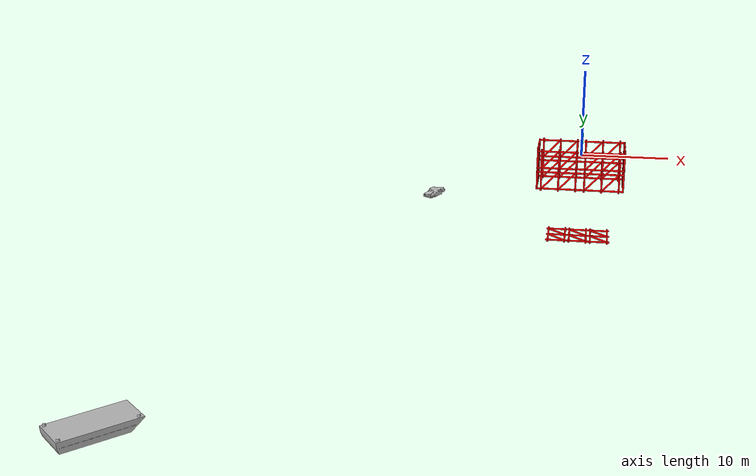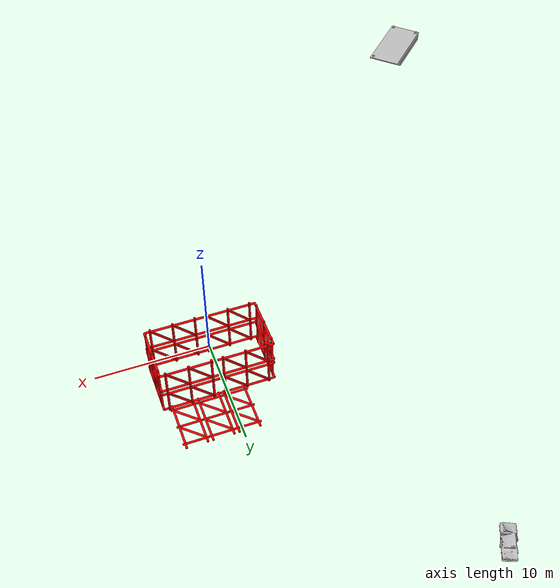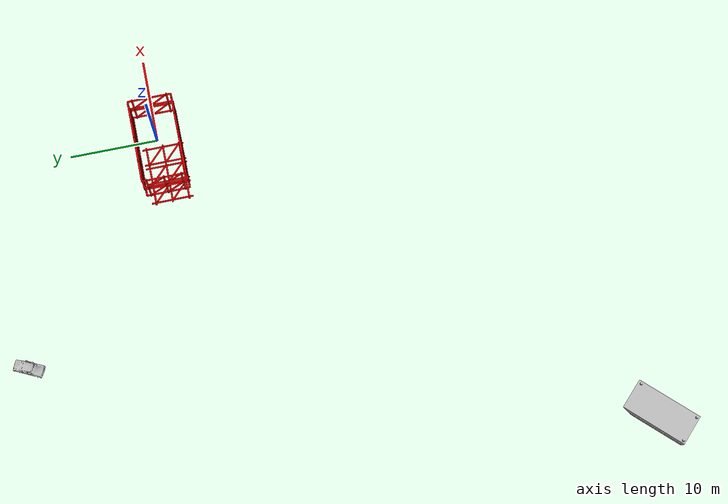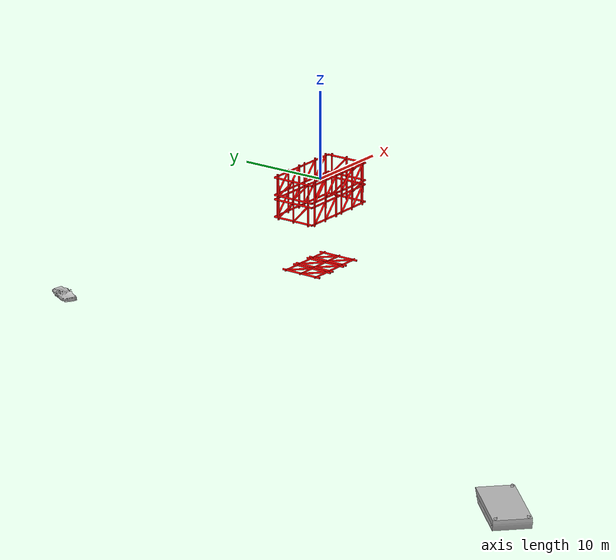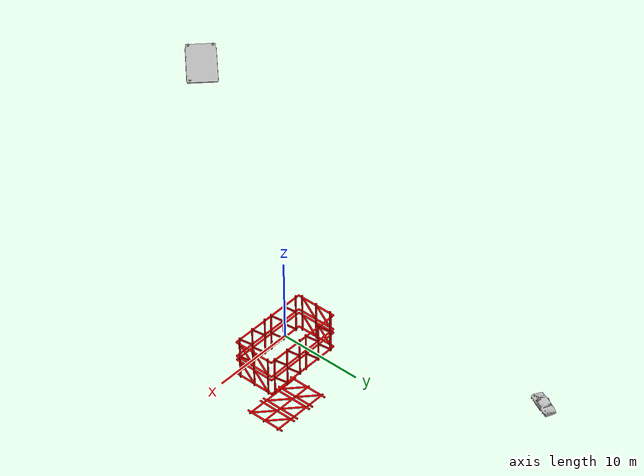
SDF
<sdf version="1.6">
 <world name="wrecks">
  <include><uri>model://jequitaia_ferry</uri><pose>-40 -50 -12.4 0 0 -0.785</pose></include>
  <include><uri>model://car</uri><name>car</name><pose>-20 20 -11.9 0 0 0</pose></include>
  <include><name>mega_structure</name><uri>model://mega_structure</uri></include>
 </world>
</sdf>

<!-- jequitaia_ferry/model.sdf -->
<sdf version="1.4">
    <model name="jequitaia_ferry">
        <pose>0 0 0 0 0 0</pose>
        <static>true</static>
        <link name="jequitaia_ferry_body">
            <visual name="visual">
                <geometry>
                    <mesh>
                        <uri>model://jequitaia_ferry/visual.osgb</uri>
                    </mesh>
                </geometry>
            </visual>
            <collision name="collision">
                <geometry>
                    <mesh>
                        <uri>model://jequitaia_ferry/collision.stl</uri>
                    </mesh>
                </geometry>
            </collision>
            <inertial>
                <pose>0 0 -1 0 0 0</pose>
                <inertia>
                    <ixx>0.0</ixx>
                    <ixy>0</ixy>
                    <ixz>0.0</ixz>
                    <iyy>0.0</iyy>
                    <iyz>0</iyz>
                    <izz>0.0</izz>
                </inertia>
                <mass>1.0</mass>
            </inertial>
        </link>
    </model>
</sdf>

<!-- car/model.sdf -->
<sdf version="1.4">
    <model name="car">
        <pose>0 0 0 0 0 0</pose>
        <static>true</static>
        <link name="car_body">
            <visual name="visual">
                <geometry>
                    <mesh>
                        <uri>model://car/visual.osgb</uri>
                    </mesh>
                </geometry>
            </visual>
            <collision name="collision">
                <geometry>
                    <mesh>
                        <uri>model://car/collision.stl</uri>
                    </mesh>
                </geometry>
            </collision>
            <inertial>
                <pose>0 0 -1 0 0 0</pose>
                <inertia>
                    <ixx>0.0</ixx>
                    <ixy>0</ixy>
                    <ixz>0.0</ixz>
                    <iyy>0.0</iyy>
                    <iyz>0</iyz>
                    <izz>0.0</izz>
                </inertia>
                <mass>1.0</mass>
            </inertial>
        </link>
    </model>
</sdf>

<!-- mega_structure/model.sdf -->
<sdf version='1.5'>
	<model name='mega_structure'>
		<static>true</static>
        <pose>5 0 0 0 0 0</pose>
		<link name='simple_structure::structure_body_01'>
			<visual name='visual01'>
				<pose>0 0 0 0 0 0</pose>
				<geometry>
					<cylinder>
						<length>2.5</length>
						<radius>0.1</radius>
					</cylinder>
				</geometry>
				<material>
					<ambient>1 0 0 1</ambient>
					<diffuse>1 0 0 1</diffuse>
					<specular>0 0 0 0</specular>
				</material>
			</visual>
			<collision name='collision01'>
				<pose>0 0 0 0 -0 0</pose>
				<geometry>
					<cylinder>
						<length>2.5</length>
						<radius>0.1</radius>
					</cylinder>
				</geometry>
				<max_contacts>10</max_contacts>
				<surface>
					<contact>
						<ode />
					</contact>
					<bounce />
					<friction>
						<ode />
					</friction>
				</surface>
			</collision>
			<visual name='visual02'>
				<pose>0 -2 0 0 -0 0</pose>
				<geometry>
					<cylinder>
						<length>2.5</length>
						<radius>0.1</radius>
					</cylinder>
				</geometry>
				<material>
					<ambient>1 0 0 1</ambient>
					<diffuse>1 0 0 1</diffuse>
					<specular>0 0 0 0</specular>
				</material>
			</visual>
			<collision name='collision02'>
				<pose>0 -2 0 0 -0 0</pose>
				<geometry>
					<cylinder>
						<length>2.5</length>
						<radius>0.1</radius>
					</cylinder>
				</geometry>
				<max_contacts>10</max_contacts>
				<surface>
					<contact>
						<ode />
					</contact>
					<bounce />
					<friction>
						<ode />
					</friction>
				</surface>
			</collision>
			<visual name='visual03'>
				<pose>0 2 0 0 -0 0</pose>
				<geometry>
					<cylinder>
						<length>2.5</length>
						<radius>0.1</radius>
					</cylinder>
				</geometry>
				<material>
					<ambient>1 0 0 1</ambient>
					<diffuse>1 0 0 1</diffuse>
					<specular>0 0 0 0</specular>
				</material>
			</visual>
			<collision name='collision03'>
				<pose>0 2 0 0 -0 0</pose>
				<geometry>
					<cylinder>
						<length>2.5</length>
						<radius>0.1</radius>
					</cylinder>
				</geometry>
				<max_contacts>10</max_contacts>
				<surface>
					<contact>
						<ode />
					</contact>
					<bounce />
					<friction>
						<ode />
					</friction>
				</surface>
			</collision>
			<visual name='visual04'>
				<pose>0 1 0 0.75 -0 0</pose>
				<geometry>
					<cylinder>
						<length>2.5</length>
						<radius>0.1</radius>
					</cylinder>
				</geometry>
				<material>
					<ambient>1 0 0 1</ambient>
					<diffuse>1 0 0 1</diffuse>
					<specular>0 0 0 0</specular>
				</material>
			</visual>
			<collision name='collision04'>
				<pose>0 1 0 0.75 -0 0</pose>
				<geometry>
					<cylinder>
						<length>2.5</length>
						<radius>0.1</radius>
					</cylinder>
				</geometry>
				<max_contacts>10</max_contacts>
				<surface>
					<contact>
						<ode />
					</contact>
					<bounce />
					<friction>
						<ode />
					</friction>
				</surface>
			</collision>
			<visual name='visual05'>
				<pose>0 -1 0 0.75 -0 0</pose>
				<geometry>
					<cylinder>
						<length>2.5</length>
						<radius>0.1</radius>
					</cylinder>
				</geometry>
				<material>
					<ambient>1 0 0 1</ambient>
					<diffuse>1 0 0 1</diffuse>
					<specular>0 0 0 0</specular>
				</material>
			</visual>
			<collision name='collision05'>
				<pose>0 -1 0 0.75 -0 0</pose>
				<geometry>
					<cylinder>
						<length>2.5</length>
						<radius>0.1</radius>
					</cylinder>
				</geometry>
				<max_contacts>10</max_contacts>
				<surface>
					<contact>
						<ode />
					</contact>
					<bounce />
					<friction>
						<ode />
					</friction>
				</surface>
			</collision>
			<visual name='visual06'>
				<pose>0 0 1 1.5707 -0 0</pose>
				<geometry>
					<cylinder>
						<length>5</length>
						<radius>0.1</radius>
					</cylinder>
				</geometry>
				<material>
					<ambient>1 0 0 1</ambient>
					<diffuse>1 0 0 1</diffuse>
					<specular>0 0 0 0</specular>
				</material>
			</visual>
			<collision name='collision06'>
				<pose>0 0 1 1.5707 -0 0</pose>
				<geometry>
					<cylinder>
						<length>2.5</length>
						<radius>0.1</radius>
					</cylinder>
				</geometry>
				<max_contacts>10</max_contacts>
				<surface>
					<contact>
						<ode />
					</contact>
					<bounce />
					<friction>
						<ode />
					</friction>
				</surface>
			</collision>
			<visual name='visual07'>
				<pose>0 0 -1 1.5707 -0 0</pose>
				<geometry>
					<cylinder>
						<length>5</length>
						<radius>0.1</radius>
					</cylinder>
				</geometry>
				<material>
					<ambient>1 0 0 1</ambient>
					<diffuse>1 0 0 1</diffuse>
					<specular>0 0 0 0</specular>
				</material>
			</visual>
			<collision name='collision07'>
				<pose>0 0 -1 1.5707 -0 0</pose>
				<geometry>
					<cylinder>
						<length>2.5</length>
						<radius>0.1</radius>
					</cylinder>
				</geometry>
				<max_contacts>10</max_contacts>
				<surface>
					<contact>
						<ode />
					</contact>
					<bounce />
					<friction>
						<ode />
					</friction>
				</surface>
			</collision>
			<velocity_decay>
				<linear>0</linear>
				<angular>0</angular>
			</velocity_decay>
			<pose>5 0 0 0 -0 0</pose>
			<self_collide>0</self_collide>
			<kinematic>0</kinematic>
			<gravity>1</gravity>
		</link>
		<static>true</static>
		<link name='simple_structure::structure_body_02'>
			<visual name='visual01'>
				<pose>0 0 0 0 -0 0</pose>
				<geometry>
					<cylinder>
						<length>2.5</length>
						<radius>0.1</radius>
					</cylinder>
				</geometry>
				<material>
					<ambient>1 0 0 1</ambient>
					<diffuse>1 0 0 1</diffuse>
					<specular>0 0 0 0</specular>
				</material>
			</visual>
			<collision name='collision01'>
				<pose>0 0 0 0 -0 0</pose>
				<geometry>
					<cylinder>
						<length>2.5</length>
						<radius>0.1</radius>
					</cylinder>
				</geometry>
				<max_contacts>10</max_contacts>
				<surface>
					<contact>
						<ode />
					</contact>
					<bounce />
					<friction>
						<ode />
					</friction>
				</surface>
			</collision>
			<visual name='visual02'>
				<pose>0 -2 0 0 -0 0</pose>
				<geometry>
					<cylinder>
						<length>2.5</length>
						<radius>0.1</radius>
					</cylinder>
				</geometry>
				<material>
					<ambient>1 0 0 1</ambient>
					<diffuse>1 0 0 1</diffuse>
					<specular>0 0 0 0</specular>
				</material>
			</visual>
			<collision name='collision02'>
				<pose>0 -2 0 0 -0 0</pose>
				<geometry>
					<cylinder>
						<length>2.5</length>
						<radius>0.1</radius>
					</cylinder>
				</geometry>
				<max_contacts>10</max_contacts>
				<surface>
					<contact>
						<ode />
					</contact>
					<bounce />
					<friction>
						<ode />
					</friction>
				</surface>
			</collision>
			<visual name='visual03'>
				<pose>0 2 0 0 -0 0</pose>
				<geometry>
					<cylinder>
						<length>2.5</length>
						<radius>0.1</radius>
					</cylinder>
				</geometry>
				<material>
					<ambient>1 0 0 1</ambient>
					<diffuse>1 0 0 1</diffuse>
					<specular>0 0 0 0</specular>
				</material>
			</visual>
			<collision name='collision03'>
				<pose>0 2 0 0 -0 0</pose>
				<geometry>
					<cylinder>
						<length>2.5</length>
						<radius>0.1</radius>
					</cylinder>
				</geometry>
				<max_contacts>10</max_contacts>
				<surface>
					<contact>
						<ode />
					</contact>
					<bounce />
					<friction>
						<ode />
					</friction>
				</surface>
			</collision>
			<visual name='visual04'>
				<pose>0 1 0 0.75 -0 0</pose>
				<geometry>
					<cylinder>
						<length>2.5</length>
						<radius>0.1</radius>
					</cylinder>
				</geometry>
				<material>
					<ambient>1 0 0 1</ambient>
					<diffuse>1 0 0 1</diffuse>
					<specular>0 0 0 0</specular>
				</material>
			</visual>
			<collision name='collision04'>
				<pose>0 1 0 0.75 -0 0</pose>
				<geometry>
					<cylinder>
						<length>2.5</length>
						<radius>0.1</radius>
					</cylinder>
				</geometry>
				<max_contacts>10</max_contacts>
				<surface>
					<contact>
						<ode />
					</contact>
					<bounce />
					<friction>
						<ode />
					</friction>
				</surface>
			</collision>
			<visual name='visual05'>
				<pose>0 -1 0 0.75 -0 0</pose>
				<geometry>
					<cylinder>
						<length>2.5</length>
						<radius>0.1</radius>
					</cylinder>
				</geometry>
				<material>
					<ambient>1 0 0 1</ambient>
					<diffuse>1 0 0 1</diffuse>
					<specular>0 0 0 0</specular>
				</material>
			</visual>
			<collision name='collision05'>
				<pose>0 -1 0 0.75 -0 0</pose>
				<geometry>
					<cylinder>
						<length>2.5</length>
						<radius>0.1</radius>
					</cylinder>
				</geometry>
				<max_contacts>10</max_contacts>
				<surface>
					<contact>
						<ode />
					</contact>
					<bounce />
					<friction>
						<ode />
					</friction>
				</surface>
			</collision>
			<visual name='visual06'>
				<pose>0 0 1 1.5707 -0 0</pose>
				<geometry>
					<cylinder>
						<length>5</length>
						<radius>0.1</radius>
					</cylinder>
				</geometry>
				<material>
					<ambient>1 0 0 1</ambient>
					<diffuse>1 0 0 1</diffuse>
					<specular>0 0 0 0</specular>
				</material>
			</visual>
			<collision name='collision06'>
				<pose>0 0 1 1.5707 -0 0</pose>
				<geometry>
					<cylinder>
						<length>2.5</length>
						<radius>0.1</radius>
					</cylinder>
				</geometry>
				<max_contacts>10</max_contacts>
				<surface>
					<contact>
						<ode />
					</contact>
					<bounce />
					<friction>
						<ode />
					</friction>
				</surface>
			</collision>
			<visual name='visual07'>
				<pose>0 0 -1 1.5707 -0 0</pose>
				<geometry>
					<cylinder>
						<length>5</length>
						<radius>0.1</radius>
					</cylinder>
				</geometry>
				<material>
					<ambient>1 0 0 1</ambient>
					<diffuse>1 0 0 1</diffuse>
					<specular>0 0 0 0</specular>
				</material>
			</visual>
			<collision name='collision07'>
				<pose>0 0 -1 1.5707 -0 0</pose>
				<geometry>
					<cylinder>
						<length>2.5</length>
						<radius>0.1</radius>
					</cylinder>
				</geometry>
				<max_contacts>10</max_contacts>
				<surface>
					<contact>
						<ode />
					</contact>
					<bounce />
					<friction>
						<ode />
					</friction>
				</surface>
			</collision>
			<velocity_decay>
				<linear>0</linear>
				<angular>0</angular>
			</velocity_decay>
			<pose>-5 0 0 0 -0 0</pose>
			<self_collide>0</self_collide>
			<kinematic>0</kinematic>
			<gravity>1</gravity>
		</link>
		<static>true</static>
		<link name='simple_structure::structure_body_03'>
			<visual name='visual01'>
				<pose>0 0 0 0 -0 0</pose>
				<geometry>
					<cylinder>
						<length>2.5</length>
						<radius>0.1</radius>
					</cylinder>
				</geometry>
				<material>
					<ambient>1 0 0 1</ambient>
					<diffuse>1 0 0 1</diffuse>
					<specular>0 0 0 0</specular>
				</material>
			</visual>
			<collision name='collision01'>
				<pose>0 0 0 0 -0 0</pose>
				<geometry>
					<cylinder>
						<length>2.5</length>
						<radius>0.1</radius>
					</cylinder>
				</geometry>
				<max_contacts>10</max_contacts>
				<surface>
					<contact>
						<ode />
					</contact>
					<bounce />
					<friction>
						<ode />
					</friction>
				</surface>
			</collision>
			<visual name='visual02'>
				<pose>0 -2 0 0 -0 0</pose>
				<geometry>
					<cylinder>
						<length>2.5</length>
						<radius>0.1</radius>
					</cylinder>
				</geometry>
				<material>
					<ambient>1 0 0 1</ambient>
					<diffuse>1 0 0 1</diffuse>
					<specular>0 0 0 0</specular>
				</material>
			</visual>
			<collision name='collision02'>
				<pose>0 -2 0 0 -0 0</pose>
				<geometry>
					<cylinder>
						<length>2.5</length>
						<radius>0.1</radius>
					</cylinder>
				</geometry>
				<max_contacts>10</max_contacts>
				<surface>
					<contact>
						<ode />
					</contact>
					<bounce />
					<friction>
						<ode />
					</friction>
				</surface>
			</collision>
			<visual name='visual03'>
				<pose>0 2 0 0 -0 0</pose>
				<geometry>
					<cylinder>
						<length>2.5</length>
						<radius>0.1</radius>
					</cylinder>
				</geometry>
				<material>
					<ambient>1 0 0 1</ambient>
					<diffuse>1 0 0 1</diffuse>
					<specular>0 0 0 0</specular>
				</material>
			</visual>
			<collision name='collision03'>
				<pose>0 2 0 0 -0 0</pose>
				<geometry>
					<cylinder>
						<length>2.5</length>
						<radius>0.1</radius>
					</cylinder>
				</geometry>
				<max_contacts>10</max_contacts>
				<surface>
					<contact>
						<ode />
					</contact>
					<bounce />
					<friction>
						<ode />
					</friction>
				</surface>
			</collision>
			<visual name='visual04'>
				<pose>0 1 0 0.75 -0 0</pose>
				<geometry>
					<cylinder>
						<length>2.5</length>
						<radius>0.1</radius>
					</cylinder>
				</geometry>
				<material>
					<ambient>1 0 0 1</ambient>
					<diffuse>1 0 0 1</diffuse>
					<specular>0 0 0 0</specular>
				</material>
			</visual>
			<collision name='collision04'>
				<pose>0 1 0 0.75 -0 0</pose>
				<geometry>
					<cylinder>
						<length>2.5</length>
						<radius>0.1</radius>
					</cylinder>
				</geometry>
				<max_contacts>10</max_contacts>
				<surface>
					<contact>
						<ode />
					</contact>
					<bounce />
					<friction>
						<ode />
					</friction>
				</surface>
			</collision>
			<visual name='visual05'>
				<pose>0 -1 0 0.75 -0 0</pose>
				<geometry>
					<cylinder>
						<length>2.5</length>
						<radius>0.1</radius>
					</cylinder>
				</geometry>
				<material>
					<ambient>1 0 0 1</ambient>
					<diffuse>1 0 0 1</diffuse>
					<specular>0 0 0 0</specular>
				</material>
			</visual>
			<collision name='collision05'>
				<pose>0 -1 0 0.75 -0 0</pose>
				<geometry>
					<cylinder>
						<length>2.5</length>
						<radius>0.1</radius>
					</cylinder>
				</geometry>
				<max_contacts>10</max_contacts>
				<surface>
					<contact>
						<ode />
					</contact>
					<bounce />
					<friction>
						<ode />
					</friction>
				</surface>
			</collision>
			<visual name='visual06'>
				<pose>0 0 1 1.5707 -0 0</pose>
				<geometry>
					<cylinder>
						<length>5</length>
						<radius>0.1</radius>
					</cylinder>
				</geometry>
				<material>
					<ambient>1 0 0 1</ambient>
					<diffuse>1 0 0 1</diffuse>
					<specular>0 0 0 0</specular>
				</material>
			</visual>
			<collision name='collision06'>
				<pose>0 0 1 1.5707 -0 0</pose>
				<geometry>
					<cylinder>
						<length>2.5</length>
						<radius>0.1</radius>
					</cylinder>
				</geometry>
				<max_contacts>10</max_contacts>
				<surface>
					<contact>
						<ode />
					</contact>
					<bounce />
					<friction>
						<ode />
					</friction>
				</surface>
			</collision>
			<visual name='visual07'>
				<pose>0 0 -1 1.5707 -0 0</pose>
				<geometry>
					<cylinder>
						<length>5</length>
						<radius>0.1</radius>
					</cylinder>
				</geometry>
				<material>
					<ambient>1 0 0 1</ambient>
					<diffuse>1 0 0 1</diffuse>
					<specular>0 0 0 0</specular>
				</material>
			</visual>
			<collision name='collision07'>
				<pose>0 0 -1 1.5707 -0 0</pose>
				<geometry>
					<cylinder>
						<length>2.5</length>
						<radius>0.1</radius>
					</cylinder>
				</geometry>
				<max_contacts>10</max_contacts>
				<surface>
					<contact>
						<ode />
					</contact>
					<bounce />
					<friction>
						<ode />
					</friction>
				</surface>
			</collision>
			<velocity_decay>
				<linear>0</linear>
				<angular>0</angular>
			</velocity_decay>
			<pose>2.5 2.5 0 0 -0 1.5707</pose>
			<self_collide>0</self_collide>
			<kinematic>0</kinematic>
			<gravity>1</gravity>
		</link>
		<static>true</static>
		<link name='simple_structure::structure_body_04'>
			<visual name='visual01'>
				<pose>0 0 0 0 -0 0</pose>
				<geometry>
					<cylinder>
						<length>2.5</length>
						<radius>0.1</radius>
					</cylinder>
				</geometry>
				<material>
					<ambient>1 0 0 1</ambient>
					<diffuse>1 0 0 1</diffuse>
					<specular>0 0 0 0</specular>
				</material>
			</visual>
			<collision name='collision01'>
				<pose>0 0 0 0 -0 0</pose>
				<geometry>
					<cylinder>
						<length>2.5</length>
						<radius>0.1</radius>
					</cylinder>
				</geometry>
				<max_contacts>10</max_contacts>
				<surface>
					<contact>
						<ode />
					</contact>
					<bounce />
					<friction>
						<ode />
					</friction>
				</surface>
			</collision>
			<visual name='visual02'>
				<pose>0 -2 0 0 -0 0</pose>
				<geometry>
					<cylinder>
						<length>2.5</length>
						<radius>0.1</radius>
					</cylinder>
				</geometry>
				<material>
					<ambient>1 0 0 1</ambient>
					<diffuse>1 0 0 1</diffuse>
					<specular>0 0 0 0</specular>
				</material>
			</visual>
			<collision name='collision02'>
				<pose>0 -2 0 0 -0 0</pose>
				<geometry>
					<cylinder>
						<length>2.5</length>
						<radius>0.1</radius>
					</cylinder>
				</geometry>
				<max_contacts>10</max_contacts>
				<surface>
					<contact>
						<ode />
					</contact>
					<bounce />
					<friction>
						<ode />
					</friction>
				</surface>
			</collision>
			<visual name='visual03'>
				<pose>0 2 0 0 -0 0</pose>
				<geometry>
					<cylinder>
						<length>2.5</length>
						<radius>0.1</radius>
					</cylinder>
				</geometry>
				<material>
					<ambient>1 0 0 1</ambient>
					<diffuse>1 0 0 1</diffuse>
					<specular>0 0 0 0</specular>
				</material>
			</visual>
			<collision name='collision03'>
				<pose>0 2 0 0 -0 0</pose>
				<geometry>
					<cylinder>
						<length>2.5</length>
						<radius>0.1</radius>
					</cylinder>
				</geometry>
				<max_contacts>10</max_contacts>
				<surface>
					<contact>
						<ode />
					</contact>
					<bounce />
					<friction>
						<ode />
					</friction>
				</surface>
			</collision>
			<visual name='visual04'>
				<pose>0 1 0 0.75 -0 0</pose>
				<geometry>
					<cylinder>
						<length>2.5</length>
						<radius>0.1</radius>
					</cylinder>
				</geometry>
				<material>
					<ambient>1 0 0 1</ambient>
					<diffuse>1 0 0 1</diffuse>
					<specular>0 0 0 0</specular>
				</material>
			</visual>
			<collision name='collision04'>
				<pose>0 1 0 0.75 -0 0</pose>
				<geometry>
					<cylinder>
						<length>2.5</length>
						<radius>0.1</radius>
					</cylinder>
				</geometry>
				<max_contacts>10</max_contacts>
				<surface>
					<contact>
						<ode />
					</contact>
					<bounce />
					<friction>
						<ode />
					</friction>
				</surface>
			</collision>
			<visual name='visual05'>
				<pose>0 -1 0 0.75 -0 0</pose>
				<geometry>
					<cylinder>
						<length>2.5</length>
						<radius>0.1</radius>
					</cylinder>
				</geometry>
				<material>
					<ambient>1 0 0 1</ambient>
					<diffuse>1 0 0 1</diffuse>
					<specular>0 0 0 0</specular>
				</material>
			</visual>
			<collision name='collision05'>
				<pose>0 -1 0 0.75 -0 0</pose>
				<geometry>
					<cylinder>
						<length>2.5</length>
						<radius>0.1</radius>
					</cylinder>
				</geometry>
				<max_contacts>10</max_contacts>
				<surface>
					<contact>
						<ode />
					</contact>
					<bounce />
					<friction>
						<ode />
					</friction>
				</surface>
			</collision>
			<visual name='visual06'>
				<pose>0 0 1 1.5707 -0 0</pose>
				<geometry>
					<cylinder>
						<length>5</length>
						<radius>0.1</radius>
					</cylinder>
				</geometry>
				<material>
					<ambient>1 0 0 1</ambient>
					<diffuse>1 0 0 1</diffuse>
					<specular>0 0 0 0</specular>
				</material>
			</visual>
			<collision name='collision06'>
				<pose>0 0 1 1.5707 -0 0</pose>
				<geometry>
					<cylinder>
						<length>2.5</length>
						<radius>0.1</radius>
					</cylinder>
				</geometry>
				<max_contacts>10</max_contacts>
				<surface>
					<contact>
						<ode />
					</contact>
					<bounce />
					<friction>
						<ode />
					</friction>
				</surface>
			</collision>
			<visual name='visual07'>
				<pose>0 0 -1 1.5707 -0 0</pose>
				<geometry>
					<cylinder>
						<length>5</length>
						<radius>0.1</radius>
					</cylinder>
				</geometry>
				<material>
					<ambient>1 0 0 1</ambient>
					<diffuse>1 0 0 1</diffuse>
					<specular>0 0 0 0</specular>
				</material>
			</visual>
			<collision name='collision07'>
				<pose>0 0 -1 1.5707 -0 0</pose>
				<geometry>
					<cylinder>
						<length>2.5</length>
						<radius>0.1</radius>
					</cylinder>
				</geometry>
				<max_contacts>10</max_contacts>
				<surface>
					<contact>
						<ode />
					</contact>
					<bounce />
					<friction>
						<ode />
					</friction>
				</surface>
			</collision>
			<velocity_decay>
				<linear>0</linear>
				<angular>0</angular>
			</velocity_decay>
			<pose>-2.5 2.5 0 0 -0 1.5707</pose>
			<self_collide>0</self_collide>
			<kinematic>0</kinematic>
			<gravity>1</gravity>
		</link>
		<static>true</static>
		<link name='simple_structure::structure_body_05'>
			<visual name='visual01'>
				<pose>0 0 0 0 -0 0</pose>
				<geometry>
					<cylinder>
						<length>2.5</length>
						<radius>0.1</radius>
					</cylinder>
				</geometry>
				<material>
					<ambient>1 0 0 1</ambient>
					<diffuse>1 0 0 1</diffuse>
					<specular>0 0 0 0</specular>
				</material>
			</visual>
			<collision name='collision01'>
				<pose>0 0 0 0 -0 0</pose>
				<geometry>
					<cylinder>
						<length>2.5</length>
						<radius>0.1</radius>
					</cylinder>
				</geometry>
				<max_contacts>10</max_contacts>
				<surface>
					<contact>
						<ode />
					</contact>
					<bounce />
					<friction>
						<ode />
					</friction>
				</surface>
			</collision>
			<visual name='visual02'>
				<pose>0 -2 0 0 -0 0</pose>
				<geometry>
					<cylinder>
						<length>2.5</length>
						<radius>0.1</radius>
					</cylinder>
				</geometry>
				<material>
					<ambient>1 0 0 1</ambient>
					<diffuse>1 0 0 1</diffuse>
					<specular>0 0 0 0</specular>
				</material>
			</visual>
			<collision name='collision02'>
				<pose>0 -2 0 0 -0 0</pose>
				<geometry>
					<cylinder>
						<length>2.5</length>
						<radius>0.1</radius>
					</cylinder>
				</geometry>
				<max_contacts>10</max_contacts>
				<surface>
					<contact>
						<ode />
					</contact>
					<bounce />
					<friction>
						<ode />
					</friction>
				</surface>
			</collision>
			<visual name='visual03'>
				<pose>0 2 0 0 -0 0</pose>
				<geometry>
					<cylinder>
						<length>2.5</length>
						<radius>0.1</radius>
					</cylinder>
				</geometry>
				<material>
					<ambient>1 0 0 1</ambient>
					<diffuse>1 0 0 1</diffuse>
					<specular>0 0 0 0</specular>
				</material>
			</visual>
			<collision name='collision03'>
				<pose>0 2 0 0 -0 0</pose>
				<geometry>
					<cylinder>
						<length>2.5</length>
						<radius>0.1</radius>
					</cylinder>
				</geometry>
				<max_contacts>10</max_contacts>
				<surface>
					<contact>
						<ode />
					</contact>
					<bounce />
					<friction>
						<ode />
					</friction>
				</surface>
			</collision>
			<visual name='visual04'>
				<pose>0 1 0 0.75 -0 0</pose>
				<geometry>
					<cylinder>
						<length>2.5</length>
						<radius>0.1</radius>
					</cylinder>
				</geometry>
				<material>
					<ambient>1 0 0 1</ambient>
					<diffuse>1 0 0 1</diffuse>
					<specular>0 0 0 0</specular>
				</material>
			</visual>
			<collision name='collision04'>
				<pose>0 1 0 0.75 -0 0</pose>
				<geometry>
					<cylinder>
						<length>2.5</length>
						<radius>0.1</radius>
					</cylinder>
				</geometry>
				<max_contacts>10</max_contacts>
				<surface>
					<contact>
						<ode />
					</contact>
					<bounce />
					<friction>
						<ode />
					</friction>
				</surface>
			</collision>
			<visual name='visual05'>
				<pose>0 -1 0 0.75 -0 0</pose>
				<geometry>
					<cylinder>
						<length>2.5</length>
						<radius>0.1</radius>
					</cylinder>
				</geometry>
				<material>
					<ambient>1 0 0 1</ambient>
					<diffuse>1 0 0 1</diffuse>
					<specular>0 0 0 0</specular>
				</material>
			</visual>
			<collision name='collision05'>
				<pose>0 -1 0 0.75 -0 0</pose>
				<geometry>
					<cylinder>
						<length>2.5</length>
						<radius>0.1</radius>
					</cylinder>
				</geometry>
				<max_contacts>10</max_contacts>
				<surface>
					<contact>
						<ode />
					</contact>
					<bounce />
					<friction>
						<ode />
					</friction>
				</surface>
			</collision>
			<visual name='visual06'>
				<pose>0 0 1 1.5707 -0 0</pose>
				<geometry>
					<cylinder>
						<length>5</length>
						<radius>0.1</radius>
					</cylinder>
				</geometry>
				<material>
					<ambient>1 0 0 1</ambient>
					<diffuse>1 0 0 1</diffuse>
					<specular>0 0 0 0</specular>
				</material>
			</visual>
			<collision name='collision06'>
				<pose>0 0 1 1.5707 -0 0</pose>
				<geometry>
					<cylinder>
						<length>2.5</length>
						<radius>0.1</radius>
					</cylinder>
				</geometry>
				<max_contacts>10</max_contacts>
				<surface>
					<contact>
						<ode />
					</contact>
					<bounce />
					<friction>
						<ode />
					</friction>
				</surface>
			</collision>
			<visual name='visual07'>
				<pose>0 0 -1 1.5707 -0 0</pose>
				<geometry>
					<cylinder>
						<length>5</length>
						<radius>0.1</radius>
					</cylinder>
				</geometry>
				<material>
					<ambient>1 0 0 1</ambient>
					<diffuse>1 0 0 1</diffuse>
					<specular>0 0 0 0</specular>
				</material>
			</visual>
			<collision name='collision07'>
				<pose>0 0 -1 1.5707 -0 0</pose>
				<geometry>
					<cylinder>
						<length>2.5</length>
						<radius>0.1</radius>
					</cylinder>
				</geometry>
				<max_contacts>10</max_contacts>
				<surface>
					<contact>
						<ode />
					</contact>
					<bounce />
					<friction>
						<ode />
					</friction>
				</surface>
			</collision>
			<velocity_decay>
				<linear>0</linear>
				<angular>0</angular>
			</velocity_decay>
			<pose>2.5 -2.5 0 0 -0 1.5707</pose>
			<self_collide>0</self_collide>
			<kinematic>0</kinematic>
			<gravity>1</gravity>
		</link>
		<static>true</static>
		<link name='simple_structure::structure_body_06'>
			<visual name='visual01'>
				<pose>0 0 0 0 -0 0</pose>
				<geometry>
					<cylinder>
						<length>2.5</length>
						<radius>0.1</radius>
					</cylinder>
				</geometry>
				<material>
					<ambient>1 0 0 1</ambient>
					<diffuse>1 0 0 1</diffuse>
					<specular>0 0 0 0</specular>
				</material>
			</visual>
			<collision name='collision01'>
				<pose>0 0 0 0 -0 0</pose>
				<geometry>
					<cylinder>
						<length>2.5</length>
						<radius>0.1</radius>
					</cylinder>
				</geometry>
				<max_contacts>10</max_contacts>
				<surface>
					<contact>
						<ode />
					</contact>
					<bounce />
					<friction>
						<ode />
					</friction>
				</surface>
			</collision>
			<visual name='visual02'>
				<pose>0 -2 0 0 -0 0</pose>
				<geometry>
					<cylinder>
						<length>2.5</length>
						<radius>0.1</radius>
					</cylinder>
				</geometry>
				<material>
					<ambient>1 0 0 1</ambient>
					<diffuse>1 0 0 1</diffuse>
					<specular>0 0 0 0</specular>
				</material>
			</visual>
			<collision name='collision02'>
				<pose>0 -2 0 0 -0 0</pose>
				<geometry>
					<cylinder>
						<length>2.5</length>
						<radius>0.1</radius>
					</cylinder>
				</geometry>
				<max_contacts>10</max_contacts>
				<surface>
					<contact>
						<ode />
					</contact>
					<bounce />
					<friction>
						<ode />
					</friction>
				</surface>
			</collision>
			<visual name='visual03'>
				<pose>0 2 0 0 -0 0</pose>
				<geometry>
					<cylinder>
						<length>2.5</length>
						<radius>0.1</radius>
					</cylinder>
				</geometry>
				<material>
					<ambient>1 0 0 1</ambient>
					<diffuse>1 0 0 1</diffuse>
					<specular>0 0 0 0</specular>
				</material>
			</visual>
			<collision name='collision03'>
				<pose>0 2 0 0 -0 0</pose>
				<geometry>
					<cylinder>
						<length>2.5</length>
						<radius>0.1</radius>
					</cylinder>
				</geometry>
				<max_contacts>10</max_contacts>
				<surface>
					<contact>
						<ode />
					</contact>
					<bounce />
					<friction>
						<ode />
					</friction>
				</surface>
			</collision>
			<visual name='visual04'>
				<pose>0 1 0 0.75 -0 0</pose>
				<geometry>
					<cylinder>
						<length>2.5</length>
						<radius>0.1</radius>
					</cylinder>
				</geometry>
				<material>
					<ambient>1 0 0 1</ambient>
					<diffuse>1 0 0 1</diffuse>
					<specular>0 0 0 0</specular>
				</material>
			</visual>
			<collision name='collision04'>
				<pose>0 1 0 0.75 -0 0</pose>
				<geometry>
					<cylinder>
						<length>2.5</length>
						<radius>0.1</radius>
					</cylinder>
				</geometry>
				<max_contacts>10</max_contacts>
				<surface>
					<contact>
						<ode />
					</contact>
					<bounce />
					<friction>
						<ode />
					</friction>
				</surface>
			</collision>
			<visual name='visual05'>
				<pose>0 -1 0 0.75 -0 0</pose>
				<geometry>
					<cylinder>
						<length>2.5</length>
						<radius>0.1</radius>
					</cylinder>
				</geometry>
				<material>
					<ambient>1 0 0 1</ambient>
					<diffuse>1 0 0 1</diffuse>
					<specular>0 0 0 0</specular>
				</material>
			</visual>
			<collision name='collision05'>
				<pose>0 -1 0 0.75 -0 0</pose>
				<geometry>
					<cylinder>
						<length>2.5</length>
						<radius>0.1</radius>
					</cylinder>
				</geometry>
				<max_contacts>10</max_contacts>
				<surface>
					<contact>
						<ode />
					</contact>
					<bounce />
					<friction>
						<ode />
					</friction>
				</surface>
			</collision>
			<visual name='visual06'>
				<pose>0 0 1 1.5707 -0 0</pose>
				<geometry>
					<cylinder>
						<length>5</length>
						<radius>0.1</radius>
					</cylinder>
				</geometry>
				<material>
					<ambient>1 0 0 1</ambient>
					<diffuse>1 0 0 1</diffuse>
					<specular>0 0 0 0</specular>
				</material>
			</visual>
			<collision name='collision06'>
				<pose>0 0 1 1.5707 -0 0</pose>
				<geometry>
					<cylinder>
						<length>2.5</length>
						<radius>0.1</radius>
					</cylinder>
				</geometry>
				<max_contacts>10</max_contacts>
				<surface>
					<contact>
						<ode />
					</contact>
					<bounce />
					<friction>
						<ode />
					</friction>
				</surface>
			</collision>
			<visual name='visual07'>
				<pose>0 0 -1 1.5707 -0 0</pose>
				<geometry>
					<cylinder>
						<length>5</length>
						<radius>0.1</radius>
					</cylinder>
				</geometry>
				<material>
					<ambient>1 0 0 1</ambient>
					<diffuse>1 0 0 1</diffuse>
					<specular>0 0 0 0</specular>
				</material>
			</visual>
			<collision name='collision07'>
				<pose>0 0 -1 1.5707 -0 0</pose>
				<geometry>
					<cylinder>
						<length>2.5</length>
						<radius>0.1</radius>
					</cylinder>
				</geometry>
				<max_contacts>10</max_contacts>
				<surface>
					<contact>
						<ode />
					</contact>
					<bounce />
					<friction>
						<ode />
					</friction>
				</surface>
			</collision>
			<velocity_decay>
				<linear>0</linear>
				<angular>0</angular>
			</velocity_decay>
			<pose>-2.5 -2.5 0 0 -0 1.5707</pose>
			<self_collide>0</self_collide>
			<kinematic>0</kinematic>
			<gravity>1</gravity>
		</link>
		<static>true</static>
		<link name='simple_structure::structure_body_07'>
			<visual name='visual01'>
				<pose>0 0 0 0 -0 0</pose>
				<geometry>
					<cylinder>
						<length>2.5</length>
						<radius>0.1</radius>
					</cylinder>
				</geometry>
				<material>
					<ambient>1 0 0 1</ambient>
					<diffuse>1 0 0 1</diffuse>
					<specular>0 0 0 0</specular>
				</material>
			</visual>
			<collision name='collision01'>
				<pose>0 0 0 0 -0 0</pose>
				<geometry>
					<cylinder>
						<length>2.5</length>
						<radius>0.1</radius>
					</cylinder>
				</geometry>
				<max_contacts>10</max_contacts>
				<surface>
					<contact>
						<ode />
					</contact>
					<bounce />
					<friction>
						<ode />
					</friction>
				</surface>
			</collision>
			<visual name='visual02'>
				<pose>0 -2 0 0 -0 0</pose>
				<geometry>
					<cylinder>
						<length>2.5</length>
						<radius>0.1</radius>
					</cylinder>
				</geometry>
				<material>
					<ambient>1 0 0 1</ambient>
					<diffuse>1 0 0 1</diffuse>
					<specular>0 0 0 0</specular>
				</material>
			</visual>
			<collision name='collision02'>
				<pose>0 -2 0 0 -0 0</pose>
				<geometry>
					<cylinder>
						<length>2.5</length>
						<radius>0.1</radius>
					</cylinder>
				</geometry>
				<max_contacts>10</max_contacts>
				<surface>
					<contact>
						<ode />
					</contact>
					<bounce />
					<friction>
						<ode />
					</friction>
				</surface>
			</collision>
			<visual name='visual03'>
				<pose>0 2 0 0 -0 0</pose>
				<geometry>
					<cylinder>
						<length>2.5</length>
						<radius>0.1</radius>
					</cylinder>
				</geometry>
				<material>
					<ambient>1 0 0 1</ambient>
					<diffuse>1 0 0 1</diffuse>
					<specular>0 0 0 0</specular>
				</material>
			</visual>
			<collision name='collision03'>
				<pose>0 2 0 0 -0 0</pose>
				<geometry>
					<cylinder>
						<length>2.5</length>
						<radius>0.1</radius>
					</cylinder>
				</geometry>
				<max_contacts>10</max_contacts>
				<surface>
					<contact>
						<ode />
					</contact>
					<bounce />
					<friction>
						<ode />
					</friction>
				</surface>
			</collision>
			<visual name='visual04'>
				<pose>0 1 0 0.75 -0 0</pose>
				<geometry>
					<cylinder>
						<length>2.5</length>
						<radius>0.1</radius>
					</cylinder>
				</geometry>
				<material>
					<ambient>1 0 0 1</ambient>
					<diffuse>1 0 0 1</diffuse>
					<specular>0 0 0 0</specular>
				</material>
			</visual>
			<collision name='collision04'>
				<pose>0 1 0 0.75 -0 0</pose>
				<geometry>
					<cylinder>
						<length>2.5</length>
						<radius>0.1</radius>
					</cylinder>
				</geometry>
				<max_contacts>10</max_contacts>
				<surface>
					<contact>
						<ode />
					</contact>
					<bounce />
					<friction>
						<ode />
					</friction>
				</surface>
			</collision>
			<visual name='visual05'>
				<pose>0 -1 0 0.75 -0 0</pose>
				<geometry>
					<cylinder>
						<length>2.5</length>
						<radius>0.1</radius>
					</cylinder>
				</geometry>
				<material>
					<ambient>1 0 0 1</ambient>
					<diffuse>1 0 0 1</diffuse>
					<specular>0 0 0 0</specular>
				</material>
			</visual>
			<collision name='collision05'>
				<pose>0 -1 0 0.75 -0 0</pose>
				<geometry>
					<cylinder>
						<length>2.5</length>
						<radius>0.1</radius>
					</cylinder>
				</geometry>
				<max_contacts>10</max_contacts>
				<surface>
					<contact>
						<ode />
					</contact>
					<bounce />
					<friction>
						<ode />
					</friction>
				</surface>
			</collision>
			<visual name='visual06'>
				<pose>0 0 1 1.5707 -0 0</pose>
				<geometry>
					<cylinder>
						<length>5</length>
						<radius>0.1</radius>
					</cylinder>
				</geometry>
				<material>
					<ambient>1 0 0 1</ambient>
					<diffuse>1 0 0 1</diffuse>
					<specular>0 0 0 0</specular>
				</material>
			</visual>
			<collision name='collision06'>
				<pose>0 0 1 1.5707 -0 0</pose>
				<geometry>
					<cylinder>
						<length>2.5</length>
						<radius>0.1</radius>
					</cylinder>
				</geometry>
				<max_contacts>10</max_contacts>
				<surface>
					<contact>
						<ode />
					</contact>
					<bounce />
					<friction>
						<ode />
					</friction>
				</surface>
			</collision>
			<visual name='visual07'>
				<pose>0 0 -1 1.5707 -0 0</pose>
				<geometry>
					<cylinder>
						<length>5</length>
						<radius>0.1</radius>
					</cylinder>
				</geometry>
				<material>
					<ambient>1 0 0 1</ambient>
					<diffuse>1 0 0 1</diffuse>
					<specular>0 0 0 0</specular>
				</material>
			</visual>
			<collision name='collision07'>
				<pose>0 0 -1 1.5707 -0 0</pose>
				<geometry>
					<cylinder>
						<length>2.5</length>
						<radius>0.1</radius>
					</cylinder>
				</geometry>
				<max_contacts>10</max_contacts>
				<surface>
					<contact>
						<ode />
					</contact>
					<bounce />
					<friction>
						<ode />
					</friction>
				</surface>
			</collision>
			<velocity_decay>
				<linear>0</linear>
				<angular>0</angular>
			</velocity_decay>
			<pose>5 0 -2.5 0 -0 0</pose>
			<self_collide>0</self_collide>
			<kinematic>0</kinematic>
			<gravity>1</gravity>
		</link>
		<static>true</static>
		<link name='simple_structure::structure_body_08'>
			<visual name='visual01'>
				<pose>0 0 0 0 -0 0</pose>
				<geometry>
					<cylinder>
						<length>2.5</length>
						<radius>0.1</radius>
					</cylinder>
				</geometry>
				<material>
					<ambient>1 0 0 1</ambient>
					<diffuse>1 0 0 1</diffuse>
					<specular>0 0 0 0</specular>
				</material>
			</visual>
			<collision name='collision01'>
				<pose>0 0 0 0 -0 0</pose>
				<geometry>
					<cylinder>
						<length>2.5</length>
						<radius>0.1</radius>
					</cylinder>
				</geometry>
				<max_contacts>10</max_contacts>
				<surface>
					<contact>
						<ode />
					</contact>
					<bounce />
					<friction>
						<ode />
					</friction>
				</surface>
			</collision>
			<visual name='visual02'>
				<pose>0 -2 0 0 -0 0</pose>
				<geometry>
					<cylinder>
						<length>2.5</length>
						<radius>0.1</radius>
					</cylinder>
				</geometry>
				<material>
					<ambient>1 0 0 1</ambient>
					<diffuse>1 0 0 1</diffuse>
					<specular>0 0 0 0</specular>
				</material>
			</visual>
			<collision name='collision02'>
				<pose>0 -2 0 0 -0 0</pose>
				<geometry>
					<cylinder>
						<length>2.5</length>
						<radius>0.1</radius>
					</cylinder>
				</geometry>
				<max_contacts>10</max_contacts>
				<surface>
					<contact>
						<ode />
					</contact>
					<bounce />
					<friction>
						<ode />
					</friction>
				</surface>
			</collision>
			<visual name='visual03'>
				<pose>0 2 0 0 -0 0</pose>
				<geometry>
					<cylinder>
						<length>2.5</length>
						<radius>0.1</radius>
					</cylinder>
				</geometry>
				<material>
					<ambient>1 0 0 1</ambient>
					<diffuse>1 0 0 1</diffuse>
					<specular>0 0 0 0</specular>
				</material>
			</visual>
			<collision name='collision03'>
				<pose>0 2 0 0 -0 0</pose>
				<geometry>
					<cylinder>
						<length>2.5</length>
						<radius>0.1</radius>
					</cylinder>
				</geometry>
				<max_contacts>10</max_contacts>
				<surface>
					<contact>
						<ode />
					</contact>
					<bounce />
					<friction>
						<ode />
					</friction>
				</surface>
			</collision>
			<visual name='visual04'>
				<pose>0 1 0 0.75 -0 0</pose>
				<geometry>
					<cylinder>
						<length>2.5</length>
						<radius>0.1</radius>
					</cylinder>
				</geometry>
				<material>
					<ambient>1 0 0 1</ambient>
					<diffuse>1 0 0 1</diffuse>
					<specular>0 0 0 0</specular>
				</material>
			</visual>
			<collision name='collision04'>
				<pose>0 1 0 0.75 -0 0</pose>
				<geometry>
					<cylinder>
						<length>2.5</length>
						<radius>0.1</radius>
					</cylinder>
				</geometry>
				<max_contacts>10</max_contacts>
				<surface>
					<contact>
						<ode />
					</contact>
					<bounce />
					<friction>
						<ode />
					</friction>
				</surface>
			</collision>
			<visual name='visual05'>
				<pose>0 -1 0 0.75 -0 0</pose>
				<geometry>
					<cylinder>
						<length>2.5</length>
						<radius>0.1</radius>
					</cylinder>
				</geometry>
				<material>
					<ambient>1 0 0 1</ambient>
					<diffuse>1 0 0 1</diffuse>
					<specular>0 0 0 0</specular>
				</material>
			</visual>
			<collision name='collision05'>
				<pose>0 -1 0 0.75 -0 0</pose>
				<geometry>
					<cylinder>
						<length>2.5</length>
						<radius>0.1</radius>
					</cylinder>
				</geometry>
				<max_contacts>10</max_contacts>
				<surface>
					<contact>
						<ode />
					</contact>
					<bounce />
					<friction>
						<ode />
					</friction>
				</surface>
			</collision>
			<visual name='visual06'>
				<pose>0 0 1 1.5707 -0 0</pose>
				<geometry>
					<cylinder>
						<length>5</length>
						<radius>0.1</radius>
					</cylinder>
				</geometry>
				<material>
					<ambient>1 0 0 1</ambient>
					<diffuse>1 0 0 1</diffuse>
					<specular>0 0 0 0</specular>
				</material>
			</visual>
			<collision name='collision06'>
				<pose>0 0 1 1.5707 -0 0</pose>
				<geometry>
					<cylinder>
						<length>2.5</length>
						<radius>0.1</radius>
					</cylinder>
				</geometry>
				<max_contacts>10</max_contacts>
				<surface>
					<contact>
						<ode />
					</contact>
					<bounce />
					<friction>
						<ode />
					</friction>
				</surface>
			</collision>
			<visual name='visual07'>
				<pose>0 0 -1 1.5707 -0 0</pose>
				<geometry>
					<cylinder>
						<length>5</length>
						<radius>0.1</radius>
					</cylinder>
				</geometry>
				<material>
					<ambient>1 0 0 1</ambient>
					<diffuse>1 0 0 1</diffuse>
					<specular>0 0 0 0</specular>
				</material>
			</visual>
			<collision name='collision07'>
				<pose>0 0 -1 1.5707 -0 0</pose>
				<geometry>
					<cylinder>
						<length>2.5</length>
						<radius>0.1</radius>
					</cylinder>
				</geometry>
				<max_contacts>10</max_contacts>
				<surface>
					<contact>
						<ode />
					</contact>
					<bounce />
					<friction>
						<ode />
					</friction>
				</surface>
			</collision>
			<velocity_decay>
				<linear>0</linear>
				<angular>0</angular>
			</velocity_decay>
			<pose>-5 0 -2.5 0 -0 0</pose>
			<self_collide>0</self_collide>
			<kinematic>0</kinematic>
			<gravity>1</gravity>
		</link>
		<static>true</static>
		<link name='simple_structure::structure_body_09'>
			<visual name='visual01'>
				<pose>0 0 0 0 -0 0</pose>
				<geometry>
					<cylinder>
						<length>2.5</length>
						<radius>0.1</radius>
					</cylinder>
				</geometry>
				<material>
					<ambient>1 0 0 1</ambient>
					<diffuse>1 0 0 1</diffuse>
					<specular>0 0 0 0</specular>
				</material>
			</visual>
			<collision name='collision01'>
				<pose>0 0 0 0 -0 0</pose>
				<geometry>
					<cylinder>
						<length>2.5</length>
						<radius>0.1</radius>
					</cylinder>
				</geometry>
				<max_contacts>10</max_contacts>
				<surface>
					<contact>
						<ode />
					</contact>
					<bounce />
					<friction>
						<ode />
					</friction>
				</surface>
			</collision>
			<visual name='visual02'>
				<pose>0 -2 0 0 -0 0</pose>
				<geometry>
					<cylinder>
						<length>2.5</length>
						<radius>0.1</radius>
					</cylinder>
				</geometry>
				<material>
					<ambient>1 0 0 1</ambient>
					<diffuse>1 0 0 1</diffuse>
					<specular>0 0 0 0</specular>
				</material>
			</visual>
			<collision name='collision02'>
				<pose>0 -2 0 0 -0 0</pose>
				<geometry>
					<cylinder>
						<length>2.5</length>
						<radius>0.1</radius>
					</cylinder>
				</geometry>
				<max_contacts>10</max_contacts>
				<surface>
					<contact>
						<ode />
					</contact>
					<bounce />
					<friction>
						<ode />
					</friction>
				</surface>
			</collision>
			<visual name='visual03'>
				<pose>0 2 0 0 -0 0</pose>
				<geometry>
					<cylinder>
						<length>2.5</length>
						<radius>0.1</radius>
					</cylinder>
				</geometry>
				<material>
					<ambient>1 0 0 1</ambient>
					<diffuse>1 0 0 1</diffuse>
					<specular>0 0 0 0</specular>
				</material>
			</visual>
			<collision name='collision03'>
				<pose>0 2 0 0 -0 0</pose>
				<geometry>
					<cylinder>
						<length>2.5</length>
						<radius>0.1</radius>
					</cylinder>
				</geometry>
				<max_contacts>10</max_contacts>
				<surface>
					<contact>
						<ode />
					</contact>
					<bounce />
					<friction>
						<ode />
					</friction>
				</surface>
			</collision>
			<visual name='visual04'>
				<pose>0 1 0 0.75 -0 0</pose>
				<geometry>
					<cylinder>
						<length>2.5</length>
						<radius>0.1</radius>
					</cylinder>
				</geometry>
				<material>
					<ambient>1 0 0 1</ambient>
					<diffuse>1 0 0 1</diffuse>
					<specular>0 0 0 0</specular>
				</material>
			</visual>
			<collision name='collision04'>
				<pose>0 1 0 0.75 -0 0</pose>
				<geometry>
					<cylinder>
						<length>2.5</length>
						<radius>0.1</radius>
					</cylinder>
				</geometry>
				<max_contacts>10</max_contacts>
				<surface>
					<contact>
						<ode />
					</contact>
					<bounce />
					<friction>
						<ode />
					</friction>
				</surface>
			</collision>
			<visual name='visual05'>
				<pose>0 -1 0 0.75 -0 0</pose>
				<geometry>
					<cylinder>
						<length>2.5</length>
						<radius>0.1</radius>
					</cylinder>
				</geometry>
				<material>
					<ambient>1 0 0 1</ambient>
					<diffuse>1 0 0 1</diffuse>
					<specular>0 0 0 0</specular>
				</material>
			</visual>
			<collision name='collision05'>
				<pose>0 -1 0 0.75 -0 0</pose>
				<geometry>
					<cylinder>
						<length>2.5</length>
						<radius>0.1</radius>
					</cylinder>
				</geometry>
				<max_contacts>10</max_contacts>
				<surface>
					<contact>
						<ode />
					</contact>
					<bounce />
					<friction>
						<ode />
					</friction>
				</surface>
			</collision>
			<visual name='visual06'>
				<pose>0 0 1 1.5707 -0 0</pose>
				<geometry>
					<cylinder>
						<length>5</length>
						<radius>0.1</radius>
					</cylinder>
				</geometry>
				<material>
					<ambient>1 0 0 1</ambient>
					<diffuse>1 0 0 1</diffuse>
					<specular>0 0 0 0</specular>
				</material>
			</visual>
			<collision name='collision06'>
				<pose>0 0 1 1.5707 -0 0</pose>
				<geometry>
					<cylinder>
						<length>2.5</length>
						<radius>0.1</radius>
					</cylinder>
				</geometry>
				<max_contacts>10</max_contacts>
				<surface>
					<contact>
						<ode />
					</contact>
					<bounce />
					<friction>
						<ode />
					</friction>
				</surface>
			</collision>
			<visual name='visual07'>
				<pose>0 0 -1 1.5707 -0 0</pose>
				<geometry>
					<cylinder>
						<length>5</length>
						<radius>0.1</radius>
					</cylinder>
				</geometry>
				<material>
					<ambient>1 0 0 1</ambient>
					<diffuse>1 0 0 1</diffuse>
					<specular>0 0 0 0</specular>
				</material>
			</visual>
			<collision name='collision07'>
				<pose>0 0 -1 1.5707 -0 0</pose>
				<geometry>
					<cylinder>
						<length>2.5</length>
						<radius>0.1</radius>
					</cylinder>
				</geometry>
				<max_contacts>10</max_contacts>
				<surface>
					<contact>
						<ode />
					</contact>
					<bounce />
					<friction>
						<ode />
					</friction>
				</surface>
			</collision>
			<velocity_decay>
				<linear>0</linear>
				<angular>0</angular>
			</velocity_decay>
			<pose>2.5 2.5 -2.5 0 -0 1.5707</pose>
			<self_collide>0</self_collide>
			<kinematic>0</kinematic>
			<gravity>1</gravity>
		</link>
		<static>true</static>
		<link name='simple_structure::structure_body_10'>
			<visual name='visual01'>
				<pose>0 0 0 0 -0 0</pose>
				<geometry>
					<cylinder>
						<length>2.5</length>
						<radius>0.1</radius>
					</cylinder>
				</geometry>
				<material>
					<ambient>1 0 0 1</ambient>
					<diffuse>1 0 0 1</diffuse>
					<specular>0 0 0 0</specular>
				</material>
			</visual>
			<collision name='collision01'>
				<pose>0 0 0 0 -0 0</pose>
				<geometry>
					<cylinder>
						<length>2.5</length>
						<radius>0.1</radius>
					</cylinder>
				</geometry>
				<max_contacts>10</max_contacts>
				<surface>
					<contact>
						<ode />
					</contact>
					<bounce />
					<friction>
						<ode />
					</friction>
				</surface>
			</collision>
			<visual name='visual02'>
				<pose>0 -2 0 0 -0 0</pose>
				<geometry>
					<cylinder>
						<length>2.5</length>
						<radius>0.1</radius>
					</cylinder>
				</geometry>
				<material>
					<ambient>1 0 0 1</ambient>
					<diffuse>1 0 0 1</diffuse>
					<specular>0 0 0 0</specular>
				</material>
			</visual>
			<collision name='collision02'>
				<pose>0 -2 0 0 -0 0</pose>
				<geometry>
					<cylinder>
						<length>2.5</length>
						<radius>0.1</radius>
					</cylinder>
				</geometry>
				<max_contacts>10</max_contacts>
				<surface>
					<contact>
						<ode />
					</contact>
					<bounce />
					<friction>
						<ode />
					</friction>
				</surface>
			</collision>
			<visual name='visual03'>
				<pose>0 2 0 0 -0 0</pose>
				<geometry>
					<cylinder>
						<length>2.5</length>
						<radius>0.1</radius>
					</cylinder>
				</geometry>
				<material>
					<ambient>1 0 0 1</ambient>
					<diffuse>1 0 0 1</diffuse>
					<specular>0 0 0 0</specular>
				</material>
			</visual>
			<collision name='collision03'>
				<pose>0 2 0 0 -0 0</pose>
				<geometry>
					<cylinder>
						<length>2.5</length>
						<radius>0.1</radius>
					</cylinder>
				</geometry>
				<max_contacts>10</max_contacts>
				<surface>
					<contact>
						<ode />
					</contact>
					<bounce />
					<friction>
						<ode />
					</friction>
				</surface>
			</collision>
			<visual name='visual04'>
				<pose>0 1 0 0.75 -0 0</pose>
				<geometry>
					<cylinder>
						<length>2.5</length>
						<radius>0.1</radius>
					</cylinder>
				</geometry>
				<material>
					<ambient>1 0 0 1</ambient>
					<diffuse>1 0 0 1</diffuse>
					<specular>0 0 0 0</specular>
				</material>
			</visual>
			<collision name='collision04'>
				<pose>0 1 0 0.75 -0 0</pose>
				<geometry>
					<cylinder>
						<length>2.5</length>
						<radius>0.1</radius>
					</cylinder>
				</geometry>
				<max_contacts>10</max_contacts>
				<surface>
					<contact>
						<ode />
					</contact>
					<bounce />
					<friction>
						<ode />
					</friction>
				</surface>
			</collision>
			<visual name='visual05'>
				<pose>0 -1 0 0.75 -0 0</pose>
				<geometry>
					<cylinder>
						<length>2.5</length>
						<radius>0.1</radius>
					</cylinder>
				</geometry>
				<material>
					<ambient>1 0 0 1</ambient>
					<diffuse>1 0 0 1</diffuse>
					<specular>0 0 0 0</specular>
				</material>
			</visual>
			<collision name='collision05'>
				<pose>0 -1 0 0.75 -0 0</pose>
				<geometry>
					<cylinder>
						<length>2.5</length>
						<radius>0.1</radius>
					</cylinder>
				</geometry>
				<max_contacts>10</max_contacts>
				<surface>
					<contact>
						<ode />
					</contact>
					<bounce />
					<friction>
						<ode />
					</friction>
				</surface>
			</collision>
			<visual name='visual06'>
				<pose>0 0 1 1.5707 -0 0</pose>
				<geometry>
					<cylinder>
						<length>5</length>
						<radius>0.1</radius>
					</cylinder>
				</geometry>
				<material>
					<ambient>1 0 0 1</ambient>
					<diffuse>1 0 0 1</diffuse>
					<specular>0 0 0 0</specular>
				</material>
			</visual>
			<collision name='collision06'>
				<pose>0 0 1 1.5707 -0 0</pose>
				<geometry>
					<cylinder>
						<length>2.5</length>
						<radius>0.1</radius>
					</cylinder>
				</geometry>
				<max_contacts>10</max_contacts>
				<surface>
					<contact>
						<ode />
					</contact>
					<bounce />
					<friction>
						<ode />
					</friction>
				</surface>
			</collision>
			<visual name='visual07'>
				<pose>0 0 -1 1.5707 -0 0</pose>
				<geometry>
					<cylinder>
						<length>5</length>
						<radius>0.1</radius>
					</cylinder>
				</geometry>
				<material>
					<ambient>1 0 0 1</ambient>
					<diffuse>1 0 0 1</diffuse>
					<specular>0 0 0 0</specular>
				</material>
			</visual>
			<collision name='collision07'>
				<pose>0 0 -1 1.5707 -0 0</pose>
				<geometry>
					<cylinder>
						<length>2.5</length>
						<radius>0.1</radius>
					</cylinder>
				</geometry>
				<max_contacts>10</max_contacts>
				<surface>
					<contact>
						<ode />
					</contact>
					<bounce />
					<friction>
						<ode />
					</friction>
				</surface>
			</collision>
			<velocity_decay>
				<linear>0</linear>
				<angular>0</angular>
			</velocity_decay>
			<pose>-2.5 2.5 -2.5 0 -0 1.5707</pose>
			<self_collide>0</self_collide>
			<kinematic>0</kinematic>
			<gravity>1</gravity>
		</link>
		<static>true</static>
		<link name='simple_structure::structure_body_11'>
			<visual name='visual01'>
				<pose>0 0 0 0 -0 0</pose>
				<geometry>
					<cylinder>
						<length>2.5</length>
						<radius>0.1</radius>
					</cylinder>
				</geometry>
				<material>
					<ambient>1 0 0 1</ambient>
					<diffuse>1 0 0 1</diffuse>
					<specular>0 0 0 0</specular>
				</material>
			</visual>
			<collision name='collision01'>
				<pose>0 0 0 0 -0 0</pose>
				<geometry>
					<cylinder>
						<length>2.5</length>
						<radius>0.1</radius>
					</cylinder>
				</geometry>
				<max_contacts>10</max_contacts>
				<surface>
					<contact>
						<ode />
					</contact>
					<bounce />
					<friction>
						<ode />
					</friction>
				</surface>
			</collision>
			<visual name='visual02'>
				<pose>0 -2 0 0 -0 0</pose>
				<geometry>
					<cylinder>
						<length>2.5</length>
						<radius>0.1</radius>
					</cylinder>
				</geometry>
				<material>
					<ambient>1 0 0 1</ambient>
					<diffuse>1 0 0 1</diffuse>
					<specular>0 0 0 0</specular>
				</material>
			</visual>
			<collision name='collision02'>
				<pose>0 -2 0 0 -0 0</pose>
				<geometry>
					<cylinder>
						<length>2.5</length>
						<radius>0.1</radius>
					</cylinder>
				</geometry>
				<max_contacts>10</max_contacts>
				<surface>
					<contact>
						<ode />
					</contact>
					<bounce />
					<friction>
						<ode />
					</friction>
				</surface>
			</collision>
			<visual name='visual03'>
				<pose>0 2 0 0 -0 0</pose>
				<geometry>
					<cylinder>
						<length>2.5</length>
						<radius>0.1</radius>
					</cylinder>
				</geometry>
				<material>
					<ambient>1 0 0 1</ambient>
					<diffuse>1 0 0 1</diffuse>
					<specular>0 0 0 0</specular>
				</material>
			</visual>
			<collision name='collision03'>
				<pose>0 2 0 0 -0 0</pose>
				<geometry>
					<cylinder>
						<length>2.5</length>
						<radius>0.1</radius>
					</cylinder>
				</geometry>
				<max_contacts>10</max_contacts>
				<surface>
					<contact>
						<ode />
					</contact>
					<bounce />
					<friction>
						<ode />
					</friction>
				</surface>
			</collision>
			<visual name='visual04'>
				<pose>0 1 0 0.75 -0 0</pose>
				<geometry>
					<cylinder>
						<length>2.5</length>
						<radius>0.1</radius>
					</cylinder>
				</geometry>
				<material>
					<ambient>1 0 0 1</ambient>
					<diffuse>1 0 0 1</diffuse>
					<specular>0 0 0 0</specular>
				</material>
			</visual>
			<collision name='collision04'>
				<pose>0 1 0 0.75 -0 0</pose>
				<geometry>
					<cylinder>
						<length>2.5</length>
						<radius>0.1</radius>
					</cylinder>
				</geometry>
				<max_contacts>10</max_contacts>
				<surface>
					<contact>
						<ode />
					</contact>
					<bounce />
					<friction>
						<ode />
					</friction>
				</surface>
			</collision>
			<visual name='visual05'>
				<pose>0 -1 0 0.75 -0 0</pose>
				<geometry>
					<cylinder>
						<length>2.5</length>
						<radius>0.1</radius>
					</cylinder>
				</geometry>
				<material>
					<ambient>1 0 0 1</ambient>
					<diffuse>1 0 0 1</diffuse>
					<specular>0 0 0 0</specular>
				</material>
			</visual>
			<collision name='collision05'>
				<pose>0 -1 0 0.75 -0 0</pose>
				<geometry>
					<cylinder>
						<length>2.5</length>
						<radius>0.1</radius>
					</cylinder>
				</geometry>
				<max_contacts>10</max_contacts>
				<surface>
					<contact>
						<ode />
					</contact>
					<bounce />
					<friction>
						<ode />
					</friction>
				</surface>
			</collision>
			<visual name='visual06'>
				<pose>0 0 1 1.5707 -0 0</pose>
				<geometry>
					<cylinder>
						<length>5</length>
						<radius>0.1</radius>
					</cylinder>
				</geometry>
				<material>
					<ambient>1 0 0 1</ambient>
					<diffuse>1 0 0 1</diffuse>
					<specular>0 0 0 0</specular>
				</material>
			</visual>
			<collision name='collision06'>
				<pose>0 0 1 1.5707 -0 0</pose>
				<geometry>
					<cylinder>
						<length>2.5</length>
						<radius>0.1</radius>
					</cylinder>
				</geometry>
				<max_contacts>10</max_contacts>
				<surface>
					<contact>
						<ode />
					</contact>
					<bounce />
					<friction>
						<ode />
					</friction>
				</surface>
			</collision>
			<visual name='visual07'>
				<pose>0 0 -1 1.5707 -0 0</pose>
				<geometry>
					<cylinder>
						<length>5</length>
						<radius>0.1</radius>
					</cylinder>
				</geometry>
				<material>
					<ambient>1 0 0 1</ambient>
					<diffuse>1 0 0 1</diffuse>
					<specular>0 0 0 0</specular>
				</material>
			</visual>
			<collision name='collision07'>
				<pose>0 0 -1 1.5707 -0 0</pose>
				<geometry>
					<cylinder>
						<length>2.5</length>
						<radius>0.1</radius>
					</cylinder>
				</geometry>
				<max_contacts>10</max_contacts>
				<surface>
					<contact>
						<ode />
					</contact>
					<bounce />
					<friction>
						<ode />
					</friction>
				</surface>
			</collision>
			<velocity_decay>
				<linear>0</linear>
				<angular>0</angular>
			</velocity_decay>
			<pose>2.5 -2.5 -2.5 0 -0 1.5707</pose>
			<self_collide>0</self_collide>
			<kinematic>0</kinematic>
			<gravity>1</gravity>
		</link>
		<static>true</static>
		<link name='simple_structure::structure_body_12'>
			<visual name='visual01'>
				<pose>0 0 0 0 -0 0</pose>
				<geometry>
					<cylinder>
						<length>2.5</length>
						<radius>0.1</radius>
					</cylinder>
				</geometry>
				<material>
					<ambient>1 0 0 1</ambient>
					<diffuse>1 0 0 1</diffuse>
					<specular>0 0 0 0</specular>
				</material>
			</visual>
			<collision name='collision01'>
				<pose>0 0 0 0 -0 0</pose>
				<geometry>
					<cylinder>
						<length>2.5</length>
						<radius>0.1</radius>
					</cylinder>
				</geometry>
				<max_contacts>10</max_contacts>
				<surface>
					<contact>
						<ode />
					</contact>
					<bounce />
					<friction>
						<ode />
					</friction>
				</surface>
			</collision>
			<visual name='visual02'>
				<pose>0 -2 0 0 -0 0</pose>
				<geometry>
					<cylinder>
						<length>2.5</length>
						<radius>0.1</radius>
					</cylinder>
				</geometry>
				<material>
					<ambient>1 0 0 1</ambient>
					<diffuse>1 0 0 1</diffuse>
					<specular>0 0 0 0</specular>
				</material>
			</visual>
			<collision name='collision02'>
				<pose>0 -2 0 0 -0 0</pose>
				<geometry>
					<cylinder>
						<length>2.5</length>
						<radius>0.1</radius>
					</cylinder>
				</geometry>
				<max_contacts>10</max_contacts>
				<surface>
					<contact>
						<ode />
					</contact>
					<bounce />
					<friction>
						<ode />
					</friction>
				</surface>
			</collision>
			<visual name='visual03'>
				<pose>0 2 0 0 -0 0</pose>
				<geometry>
					<cylinder>
						<length>2.5</length>
						<radius>0.1</radius>
					</cylinder>
				</geometry>
				<material>
					<ambient>1 0 0 1</ambient>
					<diffuse>1 0 0 1</diffuse>
					<specular>0 0 0 0</specular>
				</material>
			</visual>
			<collision name='collision03'>
				<pose>0 2 0 0 -0 0</pose>
				<geometry>
					<cylinder>
						<length>2.5</length>
						<radius>0.1</radius>
					</cylinder>
				</geometry>
				<max_contacts>10</max_contacts>
				<surface>
					<contact>
						<ode />
					</contact>
					<bounce />
					<friction>
						<ode />
					</friction>
				</surface>
			</collision>
			<visual name='visual04'>
				<pose>0 1 0 0.75 -0 0</pose>
				<geometry>
					<cylinder>
						<length>2.5</length>
						<radius>0.1</radius>
					</cylinder>
				</geometry>
				<material>
					<ambient>1 0 0 1</ambient>
					<diffuse>1 0 0 1</diffuse>
					<specular>0 0 0 0</specular>
				</material>
			</visual>
			<collision name='collision04'>
				<pose>0 1 0 0.75 -0 0</pose>
				<geometry>
					<cylinder>
						<length>2.5</length>
						<radius>0.1</radius>
					</cylinder>
				</geometry>
				<max_contacts>10</max_contacts>
				<surface>
					<contact>
						<ode />
					</contact>
					<bounce />
					<friction>
						<ode />
					</friction>
				</surface>
			</collision>
			<visual name='visual05'>
				<pose>0 -1 0 0.75 -0 0</pose>
				<geometry>
					<cylinder>
						<length>2.5</length>
						<radius>0.1</radius>
					</cylinder>
				</geometry>
				<material>
					<ambient>1 0 0 1</ambient>
					<diffuse>1 0 0 1</diffuse>
					<specular>0 0 0 0</specular>
				</material>
			</visual>
			<collision name='collision05'>
				<pose>0 -1 0 0.75 -0 0</pose>
				<geometry>
					<cylinder>
						<length>2.5</length>
						<radius>0.1</radius>
					</cylinder>
				</geometry>
				<max_contacts>10</max_contacts>
				<surface>
					<contact>
						<ode />
					</contact>
					<bounce />
					<friction>
						<ode />
					</friction>
				</surface>
			</collision>
			<visual name='visual06'>
				<pose>0 0 1 1.5707 -0 0</pose>
				<geometry>
					<cylinder>
						<length>5</length>
						<radius>0.1</radius>
					</cylinder>
				</geometry>
				<material>
					<ambient>1 0 0 1</ambient>
					<diffuse>1 0 0 1</diffuse>
					<specular>0 0 0 0</specular>
				</material>
			</visual>
			<collision name='collision06'>
				<pose>0 0 1 1.5707 -0 0</pose>
				<geometry>
					<cylinder>
						<length>2.5</length>
						<radius>0.1</radius>
					</cylinder>
				</geometry>
				<max_contacts>10</max_contacts>
				<surface>
					<contact>
						<ode />
					</contact>
					<bounce />
					<friction>
						<ode />
					</friction>
				</surface>
			</collision>
			<visual name='visual07'>
				<pose>0 0 -1 1.5707 -0 0</pose>
				<geometry>
					<cylinder>
						<length>5</length>
						<radius>0.1</radius>
					</cylinder>
				</geometry>
				<material>
					<ambient>1 0 0 1</ambient>
					<diffuse>1 0 0 1</diffuse>
					<specular>0 0 0 0</specular>
				</material>
			</visual>
			<collision name='collision07'>
				<pose>0 0 -1 1.5707 -0 0</pose>
				<geometry>
					<cylinder>
						<length>2.5</length>
						<radius>0.1</radius>
					</cylinder>
				</geometry>
				<max_contacts>10</max_contacts>
				<surface>
					<contact>
						<ode />
					</contact>
					<bounce />
					<friction>
						<ode />
					</friction>
				</surface>
			</collision>
			<velocity_decay>
				<linear>0</linear>
				<angular>0</angular>
			</velocity_decay>
			<pose>-2.5 -2.5 -2.5 0 -0 1.5707</pose>
			<self_collide>0</self_collide>
			<kinematic>0</kinematic>
			<gravity>1</gravity>
		</link>
		<static>true</static>
		<link name='simple_structure::structure_body_13'>
			<visual name='visual01'>
				<pose>0 0 0 0 -0 0</pose>
				<geometry>
					<cylinder>
						<length>2.5</length>
						<radius>0.1</radius>
					</cylinder>
				</geometry>
				<material>
					<ambient>1 0 0 1</ambient>
					<diffuse>1 0 0 1</diffuse>
					<specular>0 0 0 0</specular>
				</material>
			</visual>
			<collision name='collision01'>
				<pose>0 0 0 0 -0 0</pose>
				<geometry>
					<cylinder>
						<length>2.5</length>
						<radius>0.1</radius>
					</cylinder>
				</geometry>
				<max_contacts>10</max_contacts>
				<surface>
					<contact>
						<ode />
					</contact>
					<bounce />
					<friction>
						<ode />
					</friction>
				</surface>
			</collision>
			<visual name='visual02'>
				<pose>0 -2 0 0 -0 0</pose>
				<geometry>
					<cylinder>
						<length>2.5</length>
						<radius>0.1</radius>
					</cylinder>
				</geometry>
				<material>
					<ambient>1 0 0 1</ambient>
					<diffuse>1 0 0 1</diffuse>
					<specular>0 0 0 0</specular>
				</material>
			</visual>
			<collision name='collision02'>
				<pose>0 -2 0 0 -0 0</pose>
				<geometry>
					<cylinder>
						<length>2.5</length>
						<radius>0.1</radius>
					</cylinder>
				</geometry>
				<max_contacts>10</max_contacts>
				<surface>
					<contact>
						<ode />
					</contact>
					<bounce />
					<friction>
						<ode />
					</friction>
				</surface>
			</collision>
			<visual name='visual03'>
				<pose>0 2 0 0 -0 0</pose>
				<geometry>
					<cylinder>
						<length>2.5</length>
						<radius>0.1</radius>
					</cylinder>
				</geometry>
				<material>
					<ambient>1 0 0 1</ambient>
					<diffuse>1 0 0 1</diffuse>
					<specular>0 0 0 0</specular>
				</material>
			</visual>
			<collision name='collision03'>
				<pose>0 2 0 0 -0 0</pose>
				<geometry>
					<cylinder>
						<length>2.5</length>
						<radius>0.1</radius>
					</cylinder>
				</geometry>
				<max_contacts>10</max_contacts>
				<surface>
					<contact>
						<ode />
					</contact>
					<bounce />
					<friction>
						<ode />
					</friction>
				</surface>
			</collision>
			<visual name='visual04'>
				<pose>0 1 0 0.75 -0 0</pose>
				<geometry>
					<cylinder>
						<length>2.5</length>
						<radius>0.1</radius>
					</cylinder>
				</geometry>
				<material>
					<ambient>1 0 0 1</ambient>
					<diffuse>1 0 0 1</diffuse>
					<specular>0 0 0 0</specular>
				</material>
			</visual>
			<collision name='collision04'>
				<pose>0 1 0 0.75 -0 0</pose>
				<geometry>
					<cylinder>
						<length>2.5</length>
						<radius>0.1</radius>
					</cylinder>
				</geometry>
				<max_contacts>10</max_contacts>
				<surface>
					<contact>
						<ode />
					</contact>
					<bounce />
					<friction>
						<ode />
					</friction>
				</surface>
			</collision>
			<visual name='visual05'>
				<pose>0 -1 0 0.75 -0 0</pose>
				<geometry>
					<cylinder>
						<length>2.5</length>
						<radius>0.1</radius>
					</cylinder>
				</geometry>
				<material>
					<ambient>1 0 0 1</ambient>
					<diffuse>1 0 0 1</diffuse>
					<specular>0 0 0 0</specular>
				</material>
			</visual>
			<collision name='collision05'>
				<pose>0 -1 0 0.75 -0 0</pose>
				<geometry>
					<cylinder>
						<length>2.5</length>
						<radius>0.1</radius>
					</cylinder>
				</geometry>
				<max_contacts>10</max_contacts>
				<surface>
					<contact>
						<ode />
					</contact>
					<bounce />
					<friction>
						<ode />
					</friction>
				</surface>
			</collision>
			<visual name='visual06'>
				<pose>0 0 1 1.5707 -0 0</pose>
				<geometry>
					<cylinder>
						<length>5</length>
						<radius>0.1</radius>
					</cylinder>
				</geometry>
				<material>
					<ambient>1 0 0 1</ambient>
					<diffuse>1 0 0 1</diffuse>
					<specular>0 0 0 0</specular>
				</material>
			</visual>
			<collision name='collision06'>
				<pose>0 0 1 1.5707 -0 0</pose>
				<geometry>
					<cylinder>
						<length>2.5</length>
						<radius>0.1</radius>
					</cylinder>
				</geometry>
				<max_contacts>10</max_contacts>
				<surface>
					<contact>
						<ode />
					</contact>
					<bounce />
					<friction>
						<ode />
					</friction>
				</surface>
			</collision>
			<visual name='visual07'>
				<pose>0 0 -1 1.5707 -0 0</pose>
				<geometry>
					<cylinder>
						<length>5</length>
						<radius>0.1</radius>
					</cylinder>
				</geometry>
				<material>
					<ambient>1 0 0 1</ambient>
					<diffuse>1 0 0 1</diffuse>
					<specular>0 0 0 0</specular>
				</material>
			</visual>
			<collision name='collision07'>
				<pose>0 0 -1 1.5707 -0 0</pose>
				<geometry>
					<cylinder>
						<length>2.5</length>
						<radius>0.1</radius>
					</cylinder>
				</geometry>
				<max_contacts>10</max_contacts>
				<surface>
					<contact>
						<ode />
					</contact>
					<bounce />
					<friction>
						<ode />
					</friction>
				</surface>
			</collision>
			<velocity_decay>
				<linear>0</linear>
				<angular>0</angular>
			</velocity_decay>
			<pose>-2.5 0 -10 0 1.5707 0</pose>
			<self_collide>0</self_collide>
			<kinematic>0</kinematic>
			<gravity>1</gravity>
		</link>
		<static>true</static>
		<link name='simple_structure::structure_body_14'>
			<visual name='visual01'>
				<pose>0 0 0 0 -0 0</pose>
				<geometry>
					<cylinder>
						<length>2.5</length>
						<radius>0.1</radius>
					</cylinder>
				</geometry>
				<material>
					<ambient>1 0 0 1</ambient>
					<diffuse>1 0 0 1</diffuse>
					<specular>0 0 0 0</specular>
				</material>
			</visual>
			<collision name='collision01'>
				<pose>0 0 0 0 -0 0</pose>
				<geometry>
					<cylinder>
						<length>2.5</length>
						<radius>0.1</radius>
					</cylinder>
				</geometry>
				<max_contacts>10</max_contacts>
				<surface>
					<contact>
						<ode />
					</contact>
					<bounce />
					<friction>
						<ode />
					</friction>
				</surface>
			</collision>
			<visual name='visual02'>
				<pose>0 -2 0 0 -0 0</pose>
				<geometry>
					<cylinder>
						<length>2.5</length>
						<radius>0.1</radius>
					</cylinder>
				</geometry>
				<material>
					<ambient>1 0 0 1</ambient>
					<diffuse>1 0 0 1</diffuse>
					<specular>0 0 0 0</specular>
				</material>
			</visual>
			<collision name='collision02'>
				<pose>0 -2 0 0 -0 0</pose>
				<geometry>
					<cylinder>
						<length>2.5</length>
						<radius>0.1</radius>
					</cylinder>
				</geometry>
				<max_contacts>10</max_contacts>
				<surface>
					<contact>
						<ode />
					</contact>
					<bounce />
					<friction>
						<ode />
					</friction>
				</surface>
			</collision>
			<visual name='visual03'>
				<pose>0 2 0 0 -0 0</pose>
				<geometry>
					<cylinder>
						<length>2.5</length>
						<radius>0.1</radius>
					</cylinder>
				</geometry>
				<material>
					<ambient>1 0 0 1</ambient>
					<diffuse>1 0 0 1</diffuse>
					<specular>0 0 0 0</specular>
				</material>
			</visual>
			<collision name='collision03'>
				<pose>0 2 0 0 -0 0</pose>
				<geometry>
					<cylinder>
						<length>2.5</length>
						<radius>0.1</radius>
					</cylinder>
				</geometry>
				<max_contacts>10</max_contacts>
				<surface>
					<contact>
						<ode />
					</contact>
					<bounce />
					<friction>
						<ode />
					</friction>
				</surface>
			</collision>
			<visual name='visual04'>
				<pose>0 1 0 0.75 -0 0</pose>
				<geometry>
					<cylinder>
						<length>2.5</length>
						<radius>0.1</radius>
					</cylinder>
				</geometry>
				<material>
					<ambient>1 0 0 1</ambient>
					<diffuse>1 0 0 1</diffuse>
					<specular>0 0 0 0</specular>
				</material>
			</visual>
			<collision name='collision04'>
				<pose>0 1 0 0.75 -0 0</pose>
				<geometry>
					<cylinder>
						<length>2.5</length>
						<radius>0.1</radius>
					</cylinder>
				</geometry>
				<max_contacts>10</max_contacts>
				<surface>
					<contact>
						<ode />
					</contact>
					<bounce />
					<friction>
						<ode />
					</friction>
				</surface>
			</collision>
			<visual name='visual05'>
				<pose>0 -1 0 0.75 -0 0</pose>
				<geometry>
					<cylinder>
						<length>2.5</length>
						<radius>0.1</radius>
					</cylinder>
				</geometry>
				<material>
					<ambient>1 0 0 1</ambient>
					<diffuse>1 0 0 1</diffuse>
					<specular>0 0 0 0</specular>
				</material>
			</visual>
			<collision name='collision05'>
				<pose>0 -1 0 0.75 -0 0</pose>
				<geometry>
					<cylinder>
						<length>2.5</length>
						<radius>0.1</radius>
					</cylinder>
				</geometry>
				<max_contacts>10</max_contacts>
				<surface>
					<contact>
						<ode />
					</contact>
					<bounce />
					<friction>
						<ode />
					</friction>
				</surface>
			</collision>
			<visual name='visual06'>
				<pose>0 0 1 1.5707 -0 0</pose>
				<geometry>
					<cylinder>
						<length>5</length>
						<radius>0.1</radius>
					</cylinder>
				</geometry>
				<material>
					<ambient>1 0 0 1</ambient>
					<diffuse>1 0 0 1</diffuse>
					<specular>0 0 0 0</specular>
				</material>
			</visual>
			<collision name='collision06'>
				<pose>0 0 1 1.5707 -0 0</pose>
				<geometry>
					<cylinder>
						<length>2.5</length>
						<radius>0.1</radius>
					</cylinder>
				</geometry>
				<max_contacts>10</max_contacts>
				<surface>
					<contact>
						<ode />
					</contact>
					<bounce />
					<friction>
						<ode />
					</friction>
				</surface>
			</collision>
			<visual name='visual07'>
				<pose>0 0 -1 1.5707 -0 0</pose>
				<geometry>
					<cylinder>
						<length>5</length>
						<radius>0.1</radius>
					</cylinder>
				</geometry>
				<material>
					<ambient>1 0 0 1</ambient>
					<diffuse>1 0 0 1</diffuse>
					<specular>0 0 0 0</specular>
				</material>
			</visual>
			<collision name='collision07'>
				<pose>0 0 -1 1.5707 -0 0</pose>
				<geometry>
					<cylinder>
						<length>2.5</length>
						<radius>0.1</radius>
					</cylinder>
				</geometry>
				<max_contacts>10</max_contacts>
				<surface>
					<contact>
						<ode />
					</contact>
					<bounce />
					<friction>
						<ode />
					</friction>
				</surface>
			</collision>
			<velocity_decay>
				<linear>0</linear>
				<angular>0</angular>
			</velocity_decay>
			<pose>0 0 -10 0 1.5707 0</pose>
			<self_collide>0</self_collide>
			<kinematic>0</kinematic>
			<gravity>1</gravity>
		</link>
		<static>true</static>
		<link name='simple_structure::structure_body_15'>
			<visual name='visual01'>
				<pose>0 0 0 0 -0 0</pose>
				<geometry>
					<cylinder>
						<length>2.5</length>
						<radius>0.1</radius>
					</cylinder>
				</geometry>
				<material>
					<ambient>1 0 0 1</ambient>
					<diffuse>1 0 0 1</diffuse>
					<specular>0 0 0 0</specular>
				</material>
			</visual>
			<collision name='collision01'>
				<pose>0 0 0 0 -0 0</pose>
				<geometry>
					<cylinder>
						<length>2.5</length>
						<radius>0.1</radius>
					</cylinder>
				</geometry>
				<max_contacts>10</max_contacts>
				<surface>
					<contact>
						<ode />
					</contact>
					<bounce />
					<friction>
						<ode />
					</friction>
				</surface>
			</collision>
			<visual name='visual02'>
				<pose>0 -2 0 0 -0 0</pose>
				<geometry>
					<cylinder>
						<length>2.5</length>
						<radius>0.1</radius>
					</cylinder>
				</geometry>
				<material>
					<ambient>1 0 0 1</ambient>
					<diffuse>1 0 0 1</diffuse>
					<specular>0 0 0 0</specular>
				</material>
			</visual>
			<collision name='collision02'>
				<pose>0 -2 0 0 -0 0</pose>
				<geometry>
					<cylinder>
						<length>2.5</length>
						<radius>0.1</radius>
					</cylinder>
				</geometry>
				<max_contacts>10</max_contacts>
				<surface>
					<contact>
						<ode />
					</contact>
					<bounce />
					<friction>
						<ode />
					</friction>
				</surface>
			</collision>
			<visual name='visual03'>
				<pose>0 2 0 0 -0 0</pose>
				<geometry>
					<cylinder>
						<length>2.5</length>
						<radius>0.1</radius>
					</cylinder>
				</geometry>
				<material>
					<ambient>1 0 0 1</ambient>
					<diffuse>1 0 0 1</diffuse>
					<specular>0 0 0 0</specular>
				</material>
			</visual>
			<collision name='collision03'>
				<pose>0 2 0 0 -0 0</pose>
				<geometry>
					<cylinder>
						<length>2.5</length>
						<radius>0.1</radius>
					</cylinder>
				</geometry>
				<max_contacts>10</max_contacts>
				<surface>
					<contact>
						<ode />
					</contact>
					<bounce />
					<friction>
						<ode />
					</friction>
				</surface>
			</collision>
			<visual name='visual04'>
				<pose>0 1 0 0.75 -0 0</pose>
				<geometry>
					<cylinder>
						<length>2.5</length>
						<radius>0.1</radius>
					</cylinder>
				</geometry>
				<material>
					<ambient>1 0 0 1</ambient>
					<diffuse>1 0 0 1</diffuse>
					<specular>0 0 0 0</specular>
				</material>
			</visual>
			<collision name='collision04'>
				<pose>0 1 0 0.75 -0 0</pose>
				<geometry>
					<cylinder>
						<length>2.5</length>
						<radius>0.1</radius>
					</cylinder>
				</geometry>
				<max_contacts>10</max_contacts>
				<surface>
					<contact>
						<ode />
					</contact>
					<bounce />
					<friction>
						<ode />
					</friction>
				</surface>
			</collision>
			<visual name='visual05'>
				<pose>0 -1 0 0.75 -0 0</pose>
				<geometry>
					<cylinder>
						<length>2.5</length>
						<radius>0.1</radius>
					</cylinder>
				</geometry>
				<material>
					<ambient>1 0 0 1</ambient>
					<diffuse>1 0 0 1</diffuse>
					<specular>0 0 0 0</specular>
				</material>
			</visual>
			<collision name='collision05'>
				<pose>0 -1 0 0.75 -0 0</pose>
				<geometry>
					<cylinder>
						<length>2.5</length>
						<radius>0.1</radius>
					</cylinder>
				</geometry>
				<max_contacts>10</max_contacts>
				<surface>
					<contact>
						<ode />
					</contact>
					<bounce />
					<friction>
						<ode />
					</friction>
				</surface>
			</collision>
			<visual name='visual06'>
				<pose>0 0 1 1.5707 -0 0</pose>
				<geometry>
					<cylinder>
						<length>5</length>
						<radius>0.1</radius>
					</cylinder>
				</geometry>
				<material>
					<ambient>1 0 0 1</ambient>
					<diffuse>1 0 0 1</diffuse>
					<specular>0 0 0 0</specular>
				</material>
			</visual>
			<collision name='collision06'>
				<pose>0 0 1 1.5707 -0 0</pose>
				<geometry>
					<cylinder>
						<length>2.5</length>
						<radius>0.1</radius>
					</cylinder>
				</geometry>
				<max_contacts>10</max_contacts>
				<surface>
					<contact>
						<ode />
					</contact>
					<bounce />
					<friction>
						<ode />
					</friction>
				</surface>
			</collision>
			<visual name='visual07'>
				<pose>0 0 -1 1.5707 -0 0</pose>
				<geometry>
					<cylinder>
						<length>5</length>
						<radius>0.1</radius>
					</cylinder>
				</geometry>
				<material>
					<ambient>1 0 0 1</ambient>
					<diffuse>1 0 0 1</diffuse>
					<specular>0 0 0 0</specular>
				</material>
			</visual>
			<collision name='collision07'>
				<pose>0 0 -1 1.5707 -0 0</pose>
				<geometry>
					<cylinder>
						<length>2.5</length>
						<radius>0.1</radius>
					</cylinder>
				</geometry>
				<max_contacts>10</max_contacts>
				<surface>
					<contact>
						<ode />
					</contact>
					<bounce />
					<friction>
						<ode />
					</friction>
				</surface>
			</collision>
			<velocity_decay>
				<linear>0</linear>
				<angular>0</angular>
			</velocity_decay>
			<pose>2.5 0 -10 0 1.5707 0</pose>
			<self_collide>0</self_collide>
			<kinematic>0</kinematic>
			<gravity>1</gravity>
		</link>
	</model>
</sdf>
